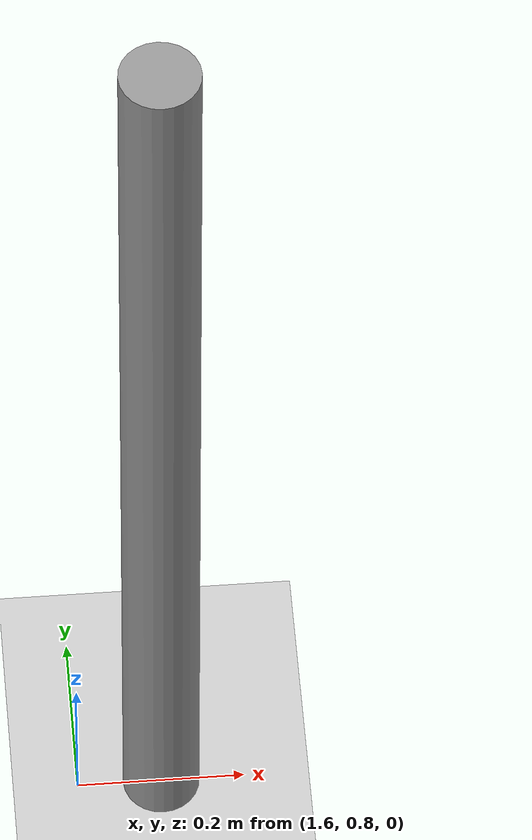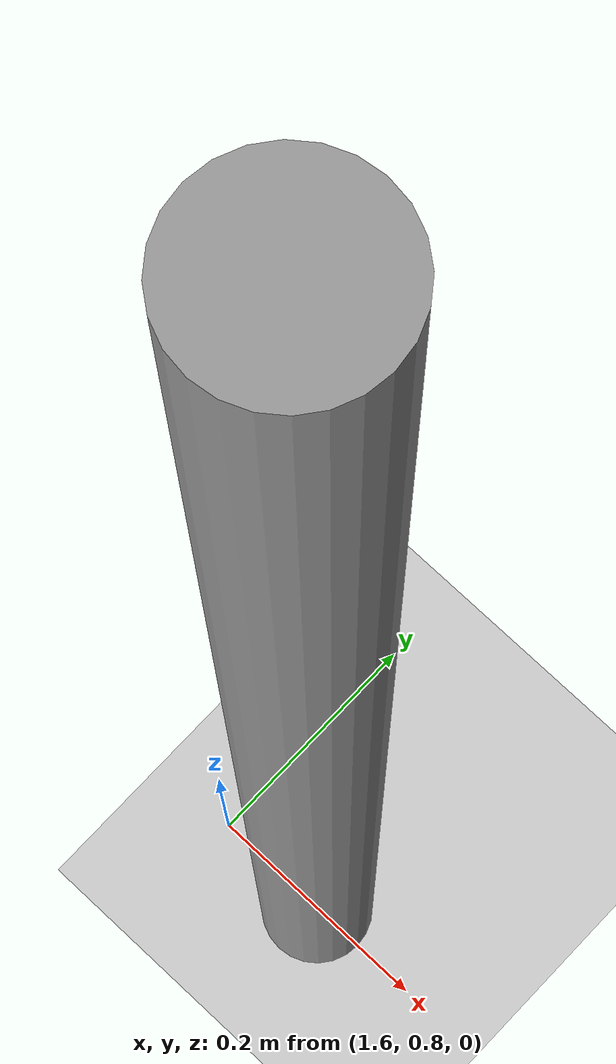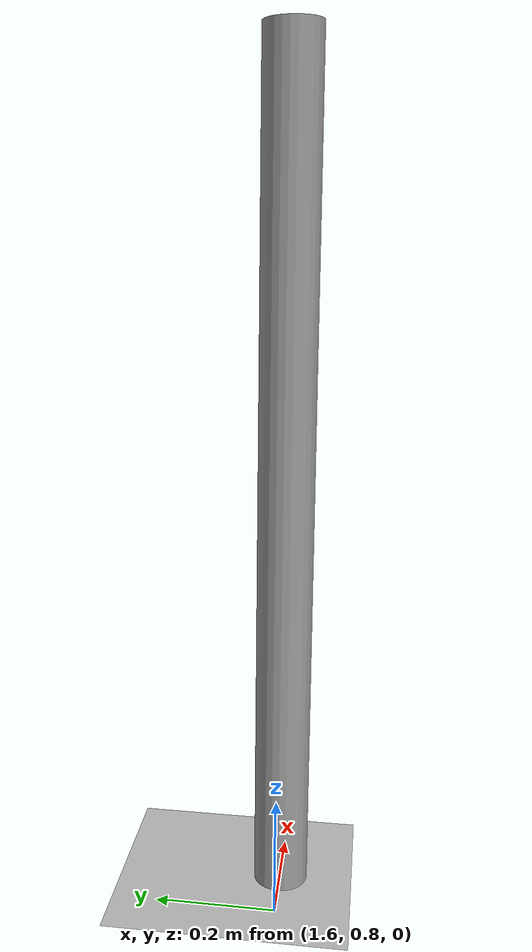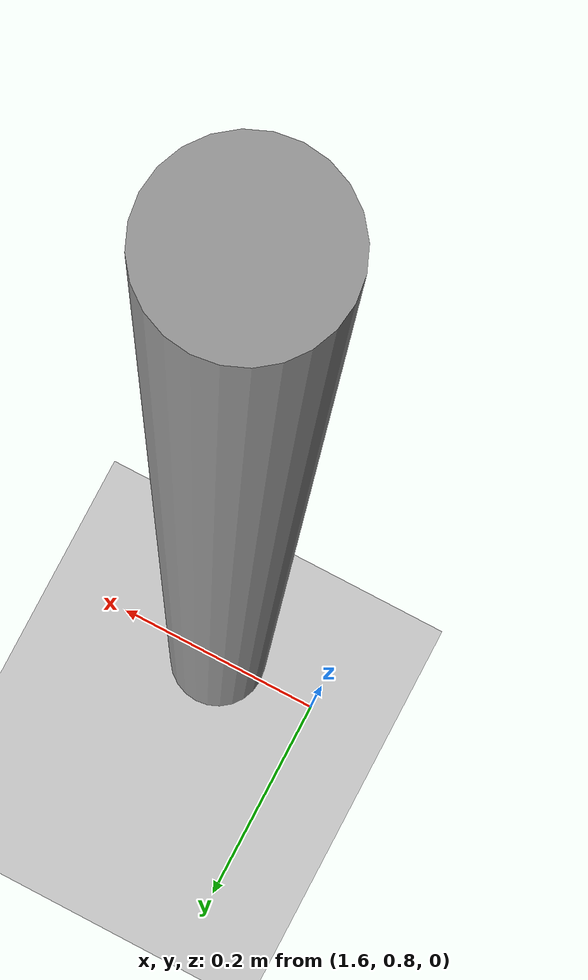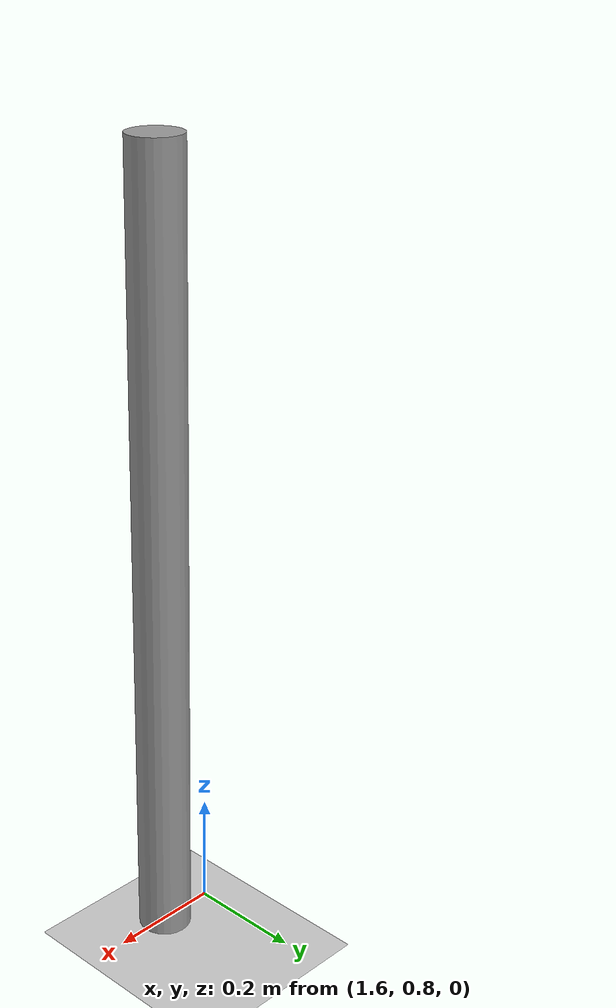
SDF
<sdf version="1.6">
 <world name="default">
  <model name="unit_cylinder_1">
   <static>0</static>
   <pose>1.7 0.8 0.691166 1e-06 5e-06 2e-06</pose>
   <link name="link">
    <inertial>
     <mass>1</mass>
     <inertia><ixz>0</ixz><ixx>1</ixx><ixy>0</ixy><izz>1</izz><iyy>1</iyy><iyz>0</iyz></inertia>
    </inertial>
    <collision name="collision">
     <geometry><cylinder><length>1.38235</length><radius>0.0456111</radius></cylinder></geometry>
    </collision>
    <visual name="visual">
     <geometry><cylinder><length>1.38235</length><radius>0.0456111</radius></cylinder></geometry>
     <material>
      <script><uri>file://media/materials/scripts/gazebo.material</uri><name>Gazebo/Grey</name></script>
     </material>
    </visual>
    <velocity_decay><linear>0</linear><angular>0</angular></velocity_decay>
   </link>
  </model>
  <model name="unit_cylinder_1">
   <static>0</static>
   <pose>1.7 0.8 0.691166 1e-06 5e-06 2e-06</pose>
   <link name="link">
    <inertial>
     <mass>1</mass>
     <inertia><ixz>0</ixz><ixx>1</ixx><ixy>0</ixy><izz>1</izz><iyy>1</iyy><iyz>0</iyz></inertia>
    </inertial>
    <collision name="collision">
     <geometry><cylinder><length>1.38235</length><radius>0.0456111</radius></cylinder></geometry>
    </collision>
    <visual name="visual">
     <geometry><cylinder><length>1.38235</length><radius>0.0456111</radius></cylinder></geometry>
     <material>
      <script><uri>file://media/materials/scripts/gazebo.material</uri><name>Gazebo/Grey</name></script>
     </material>
    </visual>
    <velocity_decay><linear>0</linear><angular>0</angular></velocity_decay>
   </link>
  </model>
  <model name="unit_cylinder_1">
   <static>0</static>
   <pose>1.7 0.8 0.691166 1e-06 5e-06 2e-06</pose>
   <link name="link">
    <inertial>
     <mass>1</mass>
     <inertia><ixz>0</ixz><ixx>1</ixx><ixy>0</ixy><izz>1</izz><iyy>1</iyy><iyz>0</iyz></inertia>
    </inertial>
    <collision name="collision">
     <geometry><cylinder><length>1.38235</length><radius>0.0456111</radius></cylinder></geometry>
    </collision>
    <visual name="visual">
     <geometry><cylinder><length>1.38235</length><radius>0.0456111</radius></cylinder></geometry>
     <material>
      <script><uri>file://media/materials/scripts/gazebo.material</uri><name>Gazebo/Grey</name></script>
     </material>
    </visual>
    <velocity_decay><linear>0</linear><angular>0</angular></velocity_decay>
   </link>
  </model>
  <model name="unit_cylinder_1">
   <static>0</static>
   <pose>1.7 0.8 0.691166 1e-06 5e-06 2e-06</pose>
   <link name="link">
    <inertial>
     <mass>1</mass>
     <inertia><ixz>0</ixz><ixx>1</ixx><ixy>0</ixy><izz>1</izz><iyy>1</iyy><iyz>0</iyz></inertia>
    </inertial>
    <collision name="collision">
     <geometry><cylinder><length>1.38235</length><radius>0.0456111</radius></cylinder></geometry>
    </collision>
    <visual name="visual">
     <geometry><cylinder><length>1.38235</length><radius>0.0456111</radius></cylinder></geometry>
     <material>
      <script><uri>file://media/materials/scripts/gazebo.material</uri><name>Gazebo/Grey</name></script>
     </material>
    </visual>
    <velocity_decay><linear>0</linear><angular>0</angular></velocity_decay>
   </link>
  </model>
  <model name="unit_cylinder_1">
   <static>0</static>
   <pose>1.7 0.8 0.691166 1e-06 5e-06 2e-06</pose>
   <link name="link">
    <inertial>
     <mass>1</mass>
     <inertia><ixz>0</ixz><ixx>1</ixx><ixy>0</ixy><izz>1</izz><iyy>1</iyy><iyz>0</iyz></inertia>
    </inertial>
    <collision name="collision">
     <geometry><cylinder><length>1.38235</length><radius>0.0456111</radius></cylinder></geometry>
    </collision>
    <visual name="visual">
     <geometry><cylinder><length>1.38235</length><radius>0.0456111</radius></cylinder></geometry>
     <material>
      <script><uri>file://media/materials/scripts/gazebo.material</uri><name>Gazebo/Grey</name></script>
     </material>
    </visual>
    <velocity_decay><linear>0</linear><angular>0</angular></velocity_decay>
   </link>
  </model>
  <model name="unit_cylinder_1">
   <static>0</static>
   <pose>1.7 0.8 0.691166 1e-06 5e-06 2e-06</pose>
   <link name="link">
    <inertial>
     <mass>1</mass>
     <inertia><ixz>0</ixz><ixx>1</ixx><ixy>0</ixy><izz>1</izz><iyy>1</iyy><iyz>0</iyz></inertia>
    </inertial>
    <collision name="collision">
     <geometry><cylinder><length>1.38235</length><radius>0.0456111</radius></cylinder></geometry>
    </collision>
    <visual name="visual">
     <geometry><cylinder><length>1.38235</length><radius>0.0456111</radius></cylinder></geometry>
     <material>
      <script><uri>file://media/materials/scripts/gazebo.material</uri><name>Gazebo/Grey</name></script>
     </material>
    </visual>
    <velocity_decay><linear>0</linear><angular>0</angular></velocity_decay>
   </link>
  </model>
  <model name="unit_cylinder_1">
   <static>0</static>
   <pose>1.7 0.8 0.691166 1e-06 5e-06 2e-06</pose>
   <link name="link">
    <inertial>
     <mass>1</mass>
     <inertia><ixz>0</ixz><ixx>1</ixx><ixy>0</ixy><izz>1</izz><iyy>1</iyy><iyz>0</iyz></inertia>
    </inertial>
    <collision name="collision">
     <geometry><cylinder><length>1.38235</length><radius>0.0456111</radius></cylinder></geometry>
    </collision>
    <visual name="visual">
     <geometry><cylinder><length>1.38235</length><radius>0.0456111</radius></cylinder></geometry>
     <material>
      <script><uri>file://media/materials/scripts/gazebo.material</uri><name>Gazebo/Grey</name></script>
     </material>
    </visual>
    <velocity_decay><linear>0</linear><angular>0</angular></velocity_decay>
   </link>
  </model>
  <model name="unit_cylinder_1">
   <static>0</static>
   <pose>1.7 0.8 0.691166 1e-06 5e-06 2e-06</pose>
   <link name="link">
    <inertial>
     <mass>1</mass>
     <inertia><ixz>0</ixz><ixx>1</ixx><ixy>0</ixy><izz>1</izz><iyy>1</iyy><iyz>0</iyz></inertia>
    </inertial>
    <collision name="collision">
     <geometry><cylinder><length>1.38235</length><radius>0.0456111</radius></cylinder></geometry>
    </collision>
    <visual name="visual">
     <geometry><cylinder><length>1.38235</length><radius>0.0456111</radius></cylinder></geometry>
     <material>
      <script><uri>file://media/materials/scripts/gazebo.material</uri><name>Gazebo/Grey</name></script>
     </material>
    </visual>
    <velocity_decay><linear>0</linear><angular>0</angular></velocity_decay>
   </link>
  </model>
  <model name="unit_cylinder_1">
   <static>0</static>
   <pose>1.7 0.8 0.691166 1e-06 5e-06 2e-06</pose>
   <link name="link">
    <inertial>
     <mass>1</mass>
     <inertia><ixz>0</ixz><ixx>1</ixx><ixy>0</ixy><izz>1</izz><iyy>1</iyy><iyz>0</iyz></inertia>
    </inertial>
    <collision name="collision">
     <geometry><cylinder><length>1.38235</length><radius>0.0456111</radius></cylinder></geometry>
    </collision>
    <visual name="visual">
     <geometry><cylinder><length>1.38235</length><radius>0.0456111</radius></cylinder></geometry>
     <material>
      <script><uri>file://media/materials/scripts/gazebo.material</uri><name>Gazebo/Grey</name></script>
     </material>
    </visual>
    <velocity_decay><linear>0</linear><angular>0</angular></velocity_decay>
   </link>
  </model>
  <model name="unit_cylinder_1">
   <static>0</static>
   <pose>1.7 0.8 0.691166 1e-06 5e-06 2e-06</pose>
   <link name="link">
    <inertial>
     <mass>1</mass>
     <inertia><ixz>0</ixz><ixx>1</ixx><ixy>0</ixy><izz>1</izz><iyy>1</iyy><iyz>0</iyz></inertia>
    </inertial>
    <collision name="collision">
     <geometry><cylinder><length>1.38235</length><radius>0.0456111</radius></cylinder></geometry>
    </collision>
    <visual name="visual">
     <geometry><cylinder><length>1.38235</length><radius>0.0456111</radius></cylinder></geometry>
     <material>
      <script><uri>file://media/materials/scripts/gazebo.material</uri><name>Gazebo/Grey</name></script>
     </material>
    </visual>
    <velocity_decay><linear>0</linear><angular>0</angular></velocity_decay>
   </link>
  </model>
  <model name="unit_cylinder_1">
   <static>0</static>
   <pose>1.7 0.8 0.691166 1e-06 5e-06 2e-06</pose>
   <link name="link">
    <inertial>
     <mass>1</mass>
     <inertia><ixz>0</ixz><ixx>1</ixx><ixy>0</ixy><izz>1</izz><iyy>1</iyy><iyz>0</iyz></inertia>
    </inertial>
    <collision name="collision">
     <geometry><cylinder><length>1.38235</length><radius>0.0456111</radius></cylinder></geometry>
    </collision>
    <visual name="visual">
     <geometry><cylinder><length>1.38235</length><radius>0.0456111</radius></cylinder></geometry>
     <material>
      <script><uri>file://media/materials/scripts/gazebo.material</uri><name>Gazebo/Grey</name></script>
     </material>
    </visual>
    <velocity_decay><linear>0</linear><angular>0</angular></velocity_decay>
   </link>
  </model>
  <model name="unit_cylinder_1">
   <static>0</static>
   <pose>1.7 0.8 0.691166 1e-06 5e-06 2e-06</pose>
   <link name="link">
    <inertial>
     <mass>1</mass>
     <inertia><ixz>0</ixz><ixx>1</ixx><ixy>0</ixy><izz>1</izz><iyy>1</iyy><iyz>0</iyz></inertia>
    </inertial>
    <collision name="collision">
     <geometry><cylinder><length>1.38235</length><radius>0.0456111</radius></cylinder></geometry>
    </collision>
    <visual name="visual">
     <geometry><cylinder><length>1.38235</length><radius>0.0456111</radius></cylinder></geometry>
     <material>
      <script><uri>file://media/materials/scripts/gazebo.material</uri><name>Gazebo/Grey</name></script>
     </material>
    </visual>
    <velocity_decay><linear>0</linear><angular>0</angular></velocity_decay>
   </link>
  </model>
  <model name="unit_cylinder_1">
   <static>0</static>
   <pose>1.7 0.8 0.691166 1e-06 5e-06 2e-06</pose>
   <link name="link">
    <inertial>
     <mass>1</mass>
     <inertia><ixz>0</ixz><ixx>1</ixx><ixy>0</ixy><izz>1</izz><iyy>1</iyy><iyz>0</iyz></inertia>
    </inertial>
    <collision name="collision">
     <geometry><cylinder><length>1.38235</length><radius>0.0456111</radius></cylinder></geometry>
    </collision>
    <visual name="visual">
     <geometry><cylinder><length>1.38235</length><radius>0.0456111</radius></cylinder></geometry>
     <material>
      <script><uri>file://media/materials/scripts/gazebo.material</uri><name>Gazebo/Grey</name></script>
     </material>
    </visual>
    <velocity_decay><linear>0</linear><angular>0</angular></velocity_decay>
   </link>
  </model>
  <model name="unit_cylinder_1">
   <static>0</static>
   <pose>1.7 0.8 0.691166 1e-06 5e-06 2e-06</pose>
   <link name="link">
    <inertial>
     <mass>1</mass>
     <inertia><ixz>0</ixz><ixx>1</ixx><ixy>0</ixy><izz>1</izz><iyy>1</iyy><iyz>0</iyz></inertia>
    </inertial>
    <collision name="collision">
     <geometry><cylinder><length>1.38235</length><radius>0.0456111</radius></cylinder></geometry>
    </collision>
    <visual name="visual">
     <geometry><cylinder><length>1.38235</length><radius>0.0456111</radius></cylinder></geometry>
     <material>
      <script><uri>file://media/materials/scripts/gazebo.material</uri><name>Gazebo/Grey</name></script>
     </material>
    </visual>
    <velocity_decay><linear>0</linear><angular>0</angular></velocity_decay>
   </link>
  </model>
  <model name="unit_cylinder_1">
   <static>0</static>
   <pose>1.7 0.8 0.691166 1e-06 5e-06 2e-06</pose>
   <link name="link">
    <inertial>
     <mass>1</mass>
     <inertia><ixz>0</ixz><ixx>1</ixx><ixy>0</ixy><izz>1</izz><iyy>1</iyy><iyz>0</iyz></inertia>
    </inertial>
    <collision name="collision">
     <geometry><cylinder><length>1.38235</length><radius>0.0456111</radius></cylinder></geometry>
    </collision>
    <visual name="visual">
     <geometry><cylinder><length>1.38235</length><radius>0.0456111</radius></cylinder></geometry>
     <material>
      <script><uri>file://media/materials/scripts/gazebo.material</uri><name>Gazebo/Grey</name></script>
     </material>
    </visual>
    <velocity_decay><linear>0</linear><angular>0</angular></velocity_decay>
   </link>
  </model>
  <model name="unit_cylinder_1">
   <static>0</static>
   <pose>1.7 0.8 0.691166 1e-06 5e-06 2e-06</pose>
   <link name="link">
    <inertial>
     <mass>1</mass>
     <inertia><ixz>0</ixz><ixx>1</ixx><ixy>0</ixy><izz>1</izz><iyy>1</iyy><iyz>0</iyz></inertia>
    </inertial>
    <collision name="collision">
     <geometry><cylinder><length>1.38235</length><radius>0.0456111</radius></cylinder></geometry>
    </collision>
    <visual name="visual">
     <geometry><cylinder><length>1.38235</length><radius>0.0456111</radius></cylinder></geometry>
     <material>
      <script><uri>file://media/materials/scripts/gazebo.material</uri><name>Gazebo/Grey</name></script>
     </material>
    </visual>
    <velocity_decay><linear>0</linear><angular>0</angular></velocity_decay>
   </link>
  </model>
  <model name="unit_cylinder_1">
   <static>0</static>
   <pose>1.7 0.8 0.691166 1e-06 5e-06 2e-06</pose>
   <link name="link">
    <inertial>
     <mass>1</mass>
     <inertia><ixz>0</ixz><ixx>1</ixx><ixy>0</ixy><izz>1</izz><iyy>1</iyy><iyz>0</iyz></inertia>
    </inertial>
    <collision name="collision">
     <geometry><cylinder><length>1.38235</length><radius>0.0456111</radius></cylinder></geometry>
    </collision>
    <visual name="visual">
     <geometry><cylinder><length>1.38235</length><radius>0.0456111</radius></cylinder></geometry>
     <material>
      <script><uri>file://media/materials/scripts/gazebo.material</uri><name>Gazebo/Grey</name></script>
     </material>
    </visual>
    <velocity_decay><linear>0</linear><angular>0</angular></velocity_decay>
   </link>
  </model>
  <model name="unit_cylinder_1">
   <static>0</static>
   <pose>1.7 0.8 0.691166 1e-06 5e-06 2e-06</pose>
   <link name="link">
    <inertial>
     <mass>1</mass>
     <inertia><ixz>0</ixz><ixx>1</ixx><ixy>0</ixy><izz>1</izz><iyy>1</iyy><iyz>0</iyz></inertia>
    </inertial>
    <collision name="collision">
     <geometry><cylinder><length>1.38235</length><radius>0.0456111</radius></cylinder></geometry>
    </collision>
    <visual name="visual">
     <geometry><cylinder><length>1.38235</length><radius>0.0456111</radius></cylinder></geometry>
     <material>
      <script><uri>file://media/materials/scripts/gazebo.material</uri><name>Gazebo/Grey</name></script>
     </material>
    </visual>
    <velocity_decay><linear>0</linear><angular>0</angular></velocity_decay>
   </link>
  </model>
  <model name="unit_cylinder_1">
   <static>0</static>
   <pose>1.7 0.8 0.691166 1e-06 5e-06 2e-06</pose>
   <link name="link">
    <inertial>
     <mass>1</mass>
     <inertia><ixz>0</ixz><ixx>1</ixx><ixy>0</ixy><izz>1</izz><iyy>1</iyy><iyz>0</iyz></inertia>
    </inertial>
    <collision name="collision">
     <geometry><cylinder><length>1.38235</length><radius>0.0456111</radius></cylinder></geometry>
    </collision>
    <visual name="visual">
     <geometry><cylinder><length>1.38235</length><radius>0.0456111</radius></cylinder></geometry>
     <material>
      <script><uri>file://media/materials/scripts/gazebo.material</uri><name>Gazebo/Grey</name></script>
     </material>
    </visual>
    <velocity_decay><linear>0</linear><angular>0</angular></velocity_decay>
   </link>
  </model>
  <model name="unit_cylinder_1">
   <static>0</static>
   <pose>1.7 0.8 0.691166 1e-06 5e-06 2e-06</pose>
   <link name="link">
    <inertial>
     <mass>1</mass>
     <inertia><ixz>0</ixz><ixx>1</ixx><ixy>0</ixy><izz>1</izz><iyy>1</iyy><iyz>0</iyz></inertia>
    </inertial>
    <collision name="collision">
     <geometry><cylinder><length>1.38235</length><radius>0.0456111</radius></cylinder></geometry>
    </collision>
    <visual name="visual">
     <geometry><cylinder><length>1.38235</length><radius>0.0456111</radius></cylinder></geometry>
     <material>
      <script><uri>file://media/materials/scripts/gazebo.material</uri><name>Gazebo/Grey</name></script>
     </material>
    </visual>
    <velocity_decay><linear>0</linear><angular>0</angular></velocity_decay>
   </link>
  </model>
  <model name="unit_cylinder_1">
   <static>0</static>
   <pose>1.7 0.8 0.691166 1e-06 5e-06 2e-06</pose>
   <link name="link">
    <inertial>
     <mass>1</mass>
     <inertia><ixz>0</ixz><ixx>1</ixx><ixy>0</ixy><izz>1</izz><iyy>1</iyy><iyz>0</iyz></inertia>
    </inertial>
    <collision name="collision">
     <geometry><cylinder><length>1.38235</length><radius>0.0456111</radius></cylinder></geometry>
    </collision>
    <visual name="visual">
     <geometry><cylinder><length>1.38235</length><radius>0.0456111</radius></cylinder></geometry>
     <material>
      <script><uri>file://media/materials/scripts/gazebo.material</uri><name>Gazebo/Grey</name></script>
     </material>
    </visual>
    <velocity_decay><linear>0</linear><angular>0</angular></velocity_decay>
   </link>
  </model>
  <model name="unit_cylinder_1">
   <static>0</static>
   <pose>1.7 0.8 0.691166 1e-06 5e-06 2e-06</pose>
   <link name="link">
    <inertial>
     <mass>1</mass>
     <inertia><ixz>0</ixz><ixx>1</ixx><ixy>0</ixy><izz>1</izz><iyy>1</iyy><iyz>0</iyz></inertia>
    </inertial>
    <collision name="collision">
     <geometry><cylinder><length>1.38235</length><radius>0.0456111</radius></cylinder></geometry>
    </collision>
    <visual name="visual">
     <geometry><cylinder><length>1.38235</length><radius>0.0456111</radius></cylinder></geometry>
     <material>
      <script><uri>file://media/materials/scripts/gazebo.material</uri><name>Gazebo/Grey</name></script>
     </material>
    </visual>
    <velocity_decay><linear>0</linear><angular>0</angular></velocity_decay>
   </link>
  </model>
  <model name="unit_cylinder_1">
   <static>0</static>
   <pose>1.7 0.8 0.691166 1e-06 5e-06 2e-06</pose>
   <link name="link">
    <inertial>
     <mass>1</mass>
     <inertia><ixz>0</ixz><ixx>1</ixx><ixy>0</ixy><izz>1</izz><iyy>1</iyy><iyz>0</iyz></inertia>
    </inertial>
    <collision name="collision">
     <geometry><cylinder><length>1.38235</length><radius>0.0456111</radius></cylinder></geometry>
    </collision>
    <visual name="visual">
     <geometry><cylinder><length>1.38235</length><radius>0.0456111</radius></cylinder></geometry>
     <material>
      <script><uri>file://media/materials/scripts/gazebo.material</uri><name>Gazebo/Grey</name></script>
     </material>
    </visual>
    <velocity_decay><linear>0</linear><angular>0</angular></velocity_decay>
   </link>
  </model>
  <model name="unit_cylinder_1">
   <static>0</static>
   <pose>1.7 0.8 0.691166 1e-06 5e-06 2e-06</pose>
   <link name="link">
    <inertial>
     <mass>1</mass>
     <inertia><ixz>0</ixz><ixx>1</ixx><ixy>0</ixy><izz>1</izz><iyy>1</iyy><iyz>0</iyz></inertia>
    </inertial>
    <collision name="collision">
     <geometry><cylinder><length>1.38235</length><radius>0.0456111</radius></cylinder></geometry>
    </collision>
    <visual name="visual">
     <geometry><cylinder><length>1.38235</length><radius>0.0456111</radius></cylinder></geometry>
     <material>
      <script><uri>file://media/materials/scripts/gazebo.material</uri><name>Gazebo/Grey</name></script>
     </material>
    </visual>
    <velocity_decay><linear>0</linear><angular>0</angular></velocity_decay>
   </link>
  </model>
  <model name="unit_cylinder_1">
   <static>0</static>
   <pose>1.7 0.8 0.691166 1e-06 5e-06 2e-06</pose>
   <link name="link">
    <inertial>
     <mass>1</mass>
     <inertia><ixz>0</ixz><ixx>1</ixx><ixy>0</ixy><izz>1</izz><iyy>1</iyy><iyz>0</iyz></inertia>
    </inertial>
    <collision name="collision">
     <geometry><cylinder><length>1.38235</length><radius>0.0456111</radius></cylinder></geometry>
    </collision>
    <visual name="visual">
     <geometry><cylinder><length>1.38235</length><radius>0.0456111</radius></cylinder></geometry>
     <material>
      <script><uri>file://media/materials/scripts/gazebo.material</uri><name>Gazebo/Grey</name></script>
     </material>
    </visual>
    <velocity_decay><linear>0</linear><angular>0</angular></velocity_decay>
   </link>
  </model>
  <model name="unit_cylinder_1">
   <static>0</static>
   <pose>1.7 0.8 0.691166 1e-06 5e-06 2e-06</pose>
   <link name="link">
    <inertial>
     <mass>1</mass>
     <inertia><ixz>0</ixz><ixx>1</ixx><ixy>0</ixy><izz>1</izz><iyy>1</iyy><iyz>0</iyz></inertia>
    </inertial>
    <collision name="collision">
     <geometry><cylinder><length>1.38235</length><radius>0.0456111</radius></cylinder></geometry>
    </collision>
    <visual name="visual">
     <geometry><cylinder><length>1.38235</length><radius>0.0456111</radius></cylinder></geometry>
     <material>
      <script><uri>file://media/materials/scripts/gazebo.material</uri><name>Gazebo/Grey</name></script>
     </material>
    </visual>
    <velocity_decay><linear>0</linear><angular>0</angular></velocity_decay>
   </link>
  </model>
  <model name="unit_cylinder_1">
   <static>0</static>
   <pose>1.7 0.8 0.691166 1e-06 5e-06 2e-06</pose>
   <link name="link">
    <inertial>
     <mass>1</mass>
     <inertia><ixz>0</ixz><ixx>1</ixx><ixy>0</ixy><izz>1</izz><iyy>1</iyy><iyz>0</iyz></inertia>
    </inertial>
    <collision name="collision">
     <geometry><cylinder><length>1.38235</length><radius>0.0456111</radius></cylinder></geometry>
    </collision>
    <visual name="visual">
     <geometry><cylinder><length>1.38235</length><radius>0.0456111</radius></cylinder></geometry>
     <material>
      <script><uri>file://media/materials/scripts/gazebo.material</uri><name>Gazebo/Grey</name></script>
     </material>
    </visual>
    <velocity_decay><linear>0</linear><angular>0</angular></velocity_decay>
   </link>
  </model>
  <model name="unit_cylinder_1">
   <static>0</static>
   <pose>1.7 0.8 0.691166 1e-06 5e-06 2e-06</pose>
   <link name="link">
    <inertial>
     <mass>1</mass>
     <inertia><ixz>0</ixz><ixx>1</ixx><ixy>0</ixy><izz>1</izz><iyy>1</iyy><iyz>0</iyz></inertia>
    </inertial>
    <collision name="collision">
     <geometry><cylinder><length>1.38235</length><radius>0.0456111</radius></cylinder></geometry>
    </collision>
    <visual name="visual">
     <geometry><cylinder><length>1.38235</length><radius>0.0456111</radius></cylinder></geometry>
     <material>
      <script><uri>file://media/materials/scripts/gazebo.material</uri><name>Gazebo/Grey</name></script>
     </material>
    </visual>
    <velocity_decay><linear>0</linear><angular>0</angular></velocity_decay>
   </link>
  </model>
  <model name="unit_cylinder_1">
   <static>0</static>
   <pose>1.7 0.8 0.691166 1e-06 5e-06 2e-06</pose>
   <link name="link">
    <inertial>
     <mass>1</mass>
     <inertia><ixz>0</ixz><ixx>1</ixx><ixy>0</ixy><izz>1</izz><iyy>1</iyy><iyz>0</iyz></inertia>
    </inertial>
    <collision name="collision">
     <geometry><cylinder><length>1.38235</length><radius>0.0456111</radius></cylinder></geometry>
    </collision>
    <visual name="visual">
     <geometry><cylinder><length>1.38235</length><radius>0.0456111</radius></cylinder></geometry>
     <material>
      <script><uri>file://media/materials/scripts/gazebo.material</uri><name>Gazebo/Grey</name></script>
     </material>
    </visual>
    <velocity_decay><linear>0</linear><angular>0</angular></velocity_decay>
   </link>
  </model>
  <model name="unit_cylinder_1">
   <static>0</static>
   <pose>1.7 0.8 0.691166 1e-06 5e-06 2e-06</pose>
   <link name="link">
    <inertial>
     <mass>1</mass>
     <inertia><ixz>0</ixz><ixx>1</ixx><ixy>0</ixy><izz>1</izz><iyy>1</iyy><iyz>0</iyz></inertia>
    </inertial>
    <collision name="collision">
     <geometry><cylinder><length>1.38235</length><radius>0.0456111</radius></cylinder></geometry>
    </collision>
    <visual name="visual">
     <geometry><cylinder><length>1.38235</length><radius>0.0456111</radius></cylinder></geometry>
     <material>
      <script><uri>file://media/materials/scripts/gazebo.material</uri><name>Gazebo/Grey</name></script>
     </material>
    </visual>
    <velocity_decay><linear>0</linear><angular>0</angular></velocity_decay>
   </link>
  </model>
  <model name="unit_cylinder_1">
   <static>0</static>
   <pose>1.7 0.8 0.691166 1e-06 5e-06 2e-06</pose>
   <link name="link">
    <inertial>
     <mass>1</mass>
     <inertia><ixz>0</ixz><ixx>1</ixx><ixy>0</ixy><izz>1</izz><iyy>1</iyy><iyz>0</iyz></inertia>
    </inertial>
    <collision name="collision">
     <geometry><cylinder><length>1.38235</length><radius>0.0456111</radius></cylinder></geometry>
    </collision>
    <visual name="visual">
     <geometry><cylinder><length>1.38235</length><radius>0.0456111</radius></cylinder></geometry>
     <material>
      <script><uri>file://media/materials/scripts/gazebo.material</uri><name>Gazebo/Grey</name></script>
     </material>
    </visual>
    <velocity_decay><linear>0</linear><angular>0</angular></velocity_decay>
   </link>
  </model>
  <model name="unit_cylinder_1">
   <static>0</static>
   <pose>1.7 0.8 0.691166 1e-06 5e-06 2e-06</pose>
   <link name="link">
    <inertial>
     <mass>1</mass>
     <inertia><ixz>0</ixz><ixx>1</ixx><ixy>0</ixy><izz>1</izz><iyy>1</iyy><iyz>0</iyz></inertia>
    </inertial>
    <collision name="collision">
     <geometry><cylinder><length>1.38235</length><radius>0.0456111</radius></cylinder></geometry>
    </collision>
    <visual name="visual">
     <geometry><cylinder><length>1.38235</length><radius>0.0456111</radius></cylinder></geometry>
     <material>
      <script><uri>file://media/materials/scripts/gazebo.material</uri><name>Gazebo/Grey</name></script>
     </material>
    </visual>
    <velocity_decay><linear>0</linear><angular>0</angular></velocity_decay>
   </link>
  </model>
  <model name="unit_cylinder_1">
   <static>0</static>
   <pose>1.7 0.8 0.691166 1e-06 5e-06 2e-06</pose>
   <link name="link">
    <inertial>
     <mass>1</mass>
     <inertia><ixz>0</ixz><ixx>1</ixx><ixy>0</ixy><izz>1</izz><iyy>1</iyy><iyz>0</iyz></inertia>
    </inertial>
    <collision name="collision">
     <geometry><cylinder><length>1.38235</length><radius>0.0456111</radius></cylinder></geometry>
    </collision>
    <visual name="visual">
     <geometry><cylinder><length>1.38235</length><radius>0.0456111</radius></cylinder></geometry>
     <material>
      <script><uri>file://media/materials/scripts/gazebo.material</uri><name>Gazebo/Grey</name></script>
     </material>
    </visual>
    <velocity_decay><linear>0</linear><angular>0</angular></velocity_decay>
   </link>
  </model>
  <model name="unit_cylinder_1">
   <static>0</static>
   <pose>1.7 0.8 0.691166 1e-06 5e-06 2e-06</pose>
   <link name="link">
    <inertial>
     <mass>1</mass>
     <inertia><ixz>0</ixz><ixx>1</ixx><ixy>0</ixy><izz>1</izz><iyy>1</iyy><iyz>0</iyz></inertia>
    </inertial>
    <collision name="collision">
     <geometry><cylinder><length>1.38235</length><radius>0.0456111</radius></cylinder></geometry>
    </collision>
    <visual name="visual">
     <geometry><cylinder><length>1.38235</length><radius>0.0456111</radius></cylinder></geometry>
     <material>
      <script><uri>file://media/materials/scripts/gazebo.material</uri><name>Gazebo/Grey</name></script>
     </material>
    </visual>
    <velocity_decay><linear>0</linear><angular>0</angular></velocity_decay>
   </link>
  </model>
  <model name="unit_cylinder_1">
   <static>0</static>
   <pose>1.7 0.8 0.691166 1e-06 5e-06 2e-06</pose>
   <link name="link">
    <inertial>
     <mass>1</mass>
     <inertia><ixz>0</ixz><ixx>1</ixx><ixy>0</ixy><izz>1</izz><iyy>1</iyy><iyz>0</iyz></inertia>
    </inertial>
    <collision name="collision">
     <geometry><cylinder><length>1.38235</length><radius>0.0456111</radius></cylinder></geometry>
    </collision>
    <visual name="visual">
     <geometry><cylinder><length>1.38235</length><radius>0.0456111</radius></cylinder></geometry>
     <material>
      <script><uri>file://media/materials/scripts/gazebo.material</uri><name>Gazebo/Grey</name></script>
     </material>
    </visual>
    <velocity_decay><linear>0</linear><angular>0</angular></velocity_decay>
   </link>
  </model>
  <model name="unit_cylinder_1">
   <static>0</static>
   <pose>1.7 0.8 0.691166 1e-06 5e-06 2e-06</pose>
   <link name="link">
    <inertial>
     <mass>1</mass>
     <inertia><ixz>0</ixz><ixx>1</ixx><ixy>0</ixy><izz>1</izz><iyy>1</iyy><iyz>0</iyz></inertia>
    </inertial>
    <collision name="collision">
     <geometry><cylinder><length>1.38235</length><radius>0.0456111</radius></cylinder></geometry>
    </collision>
    <visual name="visual">
     <geometry><cylinder><length>1.38235</length><radius>0.0456111</radius></cylinder></geometry>
     <material>
      <script><uri>file://media/materials/scripts/gazebo.material</uri><name>Gazebo/Grey</name></script>
     </material>
    </visual>
    <velocity_decay><linear>0</linear><angular>0</angular></velocity_decay>
   </link>
  </model>
  <model name="unit_cylinder_1">
   <static>0</static>
   <pose>1.7 0.8 0.691166 1e-06 5e-06 2e-06</pose>
   <link name="link">
    <inertial>
     <mass>1</mass>
     <inertia><ixz>0</ixz><ixx>1</ixx><ixy>0</ixy><izz>1</izz><iyy>1</iyy><iyz>0</iyz></inertia>
    </inertial>
    <collision name="collision">
     <geometry><cylinder><length>1.38235</length><radius>0.0456111</radius></cylinder></geometry>
    </collision>
    <visual name="visual">
     <geometry><cylinder><length>1.38235</length><radius>0.0456111</radius></cylinder></geometry>
     <material>
      <script><uri>file://media/materials/scripts/gazebo.material</uri><name>Gazebo/Grey</name></script>
     </material>
    </visual>
    <velocity_decay><linear>0</linear><angular>0</angular></velocity_decay>
   </link>
  </model>
  <model name="unit_cylinder_1">
   <static>0</static>
   <pose>1.7 0.8 0.691166 1e-06 5e-06 2e-06</pose>
   <link name="link">
    <inertial>
     <mass>1</mass>
     <inertia><ixz>0</ixz><ixx>1</ixx><ixy>0</ixy><izz>1</izz><iyy>1</iyy><iyz>0</iyz></inertia>
    </inertial>
    <collision name="collision">
     <geometry><cylinder><length>1.38235</length><radius>0.0456111</radius></cylinder></geometry>
    </collision>
    <visual name="visual">
     <geometry><cylinder><length>1.38235</length><radius>0.0456111</radius></cylinder></geometry>
     <material>
      <script><uri>file://media/materials/scripts/gazebo.material</uri><name>Gazebo/Grey</name></script>
     </material>
    </visual>
    <velocity_decay><linear>0</linear><angular>0</angular></velocity_decay>
   </link>
  </model>
  <model name="unit_cylinder_1">
   <static>0</static>
   <pose>1.7 0.8 0.691166 1e-06 5e-06 2e-06</pose>
   <link name="link">
    <inertial>
     <mass>1</mass>
     <inertia><ixz>0</ixz><ixx>1</ixx><ixy>0</ixy><izz>1</izz><iyy>1</iyy><iyz>0</iyz></inertia>
    </inertial>
    <collision name="collision">
     <geometry><cylinder><length>1.38235</length><radius>0.0456111</radius></cylinder></geometry>
    </collision>
    <visual name="visual">
     <geometry><cylinder><length>1.38235</length><radius>0.0456111</radius></cylinder></geometry>
     <material>
      <script><uri>file://media/materials/scripts/gazebo.material</uri><name>Gazebo/Grey</name></script>
     </material>
    </visual>
    <velocity_decay><linear>0</linear><angular>0</angular></velocity_decay>
   </link>
  </model>
  <model name="unit_cylinder_1">
   <static>0</static>
   <pose>1.7 0.8 0.691166 1e-06 5e-06 2e-06</pose>
   <link name="link">
    <inertial>
     <mass>1</mass>
     <inertia><ixz>0</ixz><ixx>1</ixx><ixy>0</ixy><izz>1</izz><iyy>1</iyy><iyz>0</iyz></inertia>
    </inertial>
    <collision name="collision">
     <geometry><cylinder><length>1.38235</length><radius>0.0456111</radius></cylinder></geometry>
    </collision>
    <visual name="visual">
     <geometry><cylinder><length>1.38235</length><radius>0.0456111</radius></cylinder></geometry>
     <material>
      <script><uri>file://media/materials/scripts/gazebo.material</uri><name>Gazebo/Grey</name></script>
     </material>
    </visual>
    <velocity_decay><linear>0</linear><angular>0</angular></velocity_decay>
   </link>
  </model>
  <model name="unit_cylinder_1">
   <static>0</static>
   <pose>1.7 0.8 0.691166 1e-06 5e-06 2e-06</pose>
   <link name="link">
    <inertial>
     <mass>1</mass>
     <inertia><ixz>0</ixz><ixx>1</ixx><ixy>0</ixy><izz>1</izz><iyy>1</iyy><iyz>0</iyz></inertia>
    </inertial>
    <collision name="collision">
     <geometry><cylinder><length>1.38235</length><radius>0.0456111</radius></cylinder></geometry>
    </collision>
    <visual name="visual">
     <geometry><cylinder><length>1.38235</length><radius>0.0456111</radius></cylinder></geometry>
     <material>
      <script><uri>file://media/materials/scripts/gazebo.material</uri><name>Gazebo/Grey</name></script>
     </material>
    </visual>
    <velocity_decay><linear>0</linear><angular>0</angular></velocity_decay>
   </link>
  </model>
  <model name="unit_cylinder_1">
   <static>0</static>
   <pose>1.7 0.8 0.691166 1e-06 5e-06 2e-06</pose>
   <link name="link">
    <inertial>
     <mass>1</mass>
     <inertia><ixz>0</ixz><ixx>1</ixx><ixy>0</ixy><izz>1</izz><iyy>1</iyy><iyz>0</iyz></inertia>
    </inertial>
    <collision name="collision">
     <geometry><cylinder><length>1.38235</length><radius>0.0456111</radius></cylinder></geometry>
    </collision>
    <visual name="visual">
     <geometry><cylinder><length>1.38235</length><radius>0.0456111</radius></cylinder></geometry>
     <material>
      <script><uri>file://media/materials/scripts/gazebo.material</uri><name>Gazebo/Grey</name></script>
     </material>
    </visual>
    <velocity_decay><linear>0</linear><angular>0</angular></velocity_decay>
   </link>
  </model>
  <model name="unit_cylinder_1">
   <static>0</static>
   <pose>1.7 0.8 0.691166 1e-06 5e-06 2e-06</pose>
   <link name="link">
    <inertial>
     <mass>1</mass>
     <inertia><ixz>0</ixz><ixx>1</ixx><ixy>0</ixy><izz>1</izz><iyy>1</iyy><iyz>0</iyz></inertia>
    </inertial>
    <collision name="collision">
     <geometry><cylinder><length>1.38235</length><radius>0.0456111</radius></cylinder></geometry>
    </collision>
    <visual name="visual">
     <geometry><cylinder><length>1.38235</length><radius>0.0456111</radius></cylinder></geometry>
     <material>
      <script><uri>file://media/materials/scripts/gazebo.material</uri><name>Gazebo/Grey</name></script>
     </material>
    </visual>
    <velocity_decay><linear>0</linear><angular>0</angular></velocity_decay>
   </link>
  </model>
  <model name="unit_cylinder_1">
   <static>0</static>
   <pose>1.7 0.8 0.691166 1e-06 5e-06 2e-06</pose>
   <link name="link">
    <inertial>
     <mass>1</mass>
     <inertia><ixz>0</ixz><ixx>1</ixx><ixy>0</ixy><izz>1</izz><iyy>1</iyy><iyz>0</iyz></inertia>
    </inertial>
    <collision name="collision">
     <geometry><cylinder><length>1.38235</length><radius>0.0456111</radius></cylinder></geometry>
    </collision>
    <visual name="visual">
     <geometry><cylinder><length>1.38235</length><radius>0.0456111</radius></cylinder></geometry>
     <material>
      <script><uri>file://media/materials/scripts/gazebo.material</uri><name>Gazebo/Grey</name></script>
     </material>
    </visual>
    <velocity_decay><linear>0</linear><angular>0</angular></velocity_decay>
   </link>
  </model>
  <model name="unit_cylinder_1">
   <static>0</static>
   <pose>1.7 0.8 0.691166 1e-06 5e-06 2e-06</pose>
   <link name="link">
    <inertial>
     <mass>1</mass>
     <inertia><ixz>0</ixz><ixx>1</ixx><ixy>0</ixy><izz>1</izz><iyy>1</iyy><iyz>0</iyz></inertia>
    </inertial>
    <collision name="collision">
     <geometry><cylinder><length>1.38235</length><radius>0.0456111</radius></cylinder></geometry>
    </collision>
    <visual name="visual">
     <geometry><cylinder><length>1.38235</length><radius>0.0456111</radius></cylinder></geometry>
     <material>
      <script><uri>file://media/materials/scripts/gazebo.material</uri><name>Gazebo/Grey</name></script>
     </material>
    </visual>
    <velocity_decay><linear>0</linear><angular>0</angular></velocity_decay>
   </link>
  </model>
  <model name="unit_cylinder_1">
   <static>0</static>
   <pose>1.7 0.8 0.691166 1e-06 5e-06 2e-06</pose>
   <link name="link">
    <inertial>
     <mass>1</mass>
     <inertia><ixz>0</ixz><ixx>1</ixx><ixy>0</ixy><izz>1</izz><iyy>1</iyy><iyz>0</iyz></inertia>
    </inertial>
    <collision name="collision">
     <geometry><cylinder><length>1.38235</length><radius>0.0456111</radius></cylinder></geometry>
    </collision>
    <visual name="visual">
     <geometry><cylinder><length>1.38235</length><radius>0.0456111</radius></cylinder></geometry>
     <material>
      <script><uri>file://media/materials/scripts/gazebo.material</uri><name>Gazebo/Grey</name></script>
     </material>
    </visual>
    <velocity_decay><linear>0</linear><angular>0</angular></velocity_decay>
   </link>
  </model>
  <model name="unit_cylinder_1">
   <static>0</static>
   <pose>1.7 0.8 0.691166 1e-06 5e-06 2e-06</pose>
   <link name="link">
    <inertial>
     <mass>1</mass>
     <inertia><ixz>0</ixz><ixx>1</ixx><ixy>0</ixy><izz>1</izz><iyy>1</iyy><iyz>0</iyz></inertia>
    </inertial>
    <collision name="collision">
     <geometry><cylinder><length>1.38235</length><radius>0.0456111</radius></cylinder></geometry>
    </collision>
    <visual name="visual">
     <geometry><cylinder><length>1.38235</length><radius>0.0456111</radius></cylinder></geometry>
     <material>
      <script><uri>file://media/materials/scripts/gazebo.material</uri><name>Gazebo/Grey</name></script>
     </material>
    </visual>
    <velocity_decay><linear>0</linear><angular>0</angular></velocity_decay>
   </link>
  </model>
  <model name="unit_cylinder_1">
   <static>0</static>
   <pose>1.7 0.8 0.691166 1e-06 5e-06 2e-06</pose>
   <link name="link">
    <inertial>
     <mass>1</mass>
     <inertia><ixz>0</ixz><ixx>1</ixx><ixy>0</ixy><izz>1</izz><iyy>1</iyy><iyz>0</iyz></inertia>
    </inertial>
    <collision name="collision">
     <geometry><cylinder><length>1.38235</length><radius>0.0456111</radius></cylinder></geometry>
    </collision>
    <visual name="visual">
     <geometry><cylinder><length>1.38235</length><radius>0.0456111</radius></cylinder></geometry>
     <material>
      <script><uri>file://media/materials/scripts/gazebo.material</uri><name>Gazebo/Grey</name></script>
     </material>
    </visual>
    <velocity_decay><linear>0</linear><angular>0</angular></velocity_decay>
   </link>
  </model>
  <model name="unit_cylinder_1">
   <static>0</static>
   <pose>1.7 0.8 0.691166 1e-06 5e-06 2e-06</pose>
   <link name="link">
    <inertial>
     <mass>1</mass>
     <inertia><ixz>0</ixz><ixx>1</ixx><ixy>0</ixy><izz>1</izz><iyy>1</iyy><iyz>0</iyz></inertia>
    </inertial>
    <collision name="collision">
     <geometry><cylinder><length>1.38235</length><radius>0.0456111</radius></cylinder></geometry>
    </collision>
    <visual name="visual">
     <geometry><cylinder><length>1.38235</length><radius>0.0456111</radius></cylinder></geometry>
     <material>
      <script><uri>file://media/materials/scripts/gazebo.material</uri><name>Gazebo/Grey</name></script>
     </material>
    </visual>
    <velocity_decay><linear>0</linear><angular>0</angular></velocity_decay>
   </link>
  </model>
  <model name="unit_cylinder_1">
   <static>0</static>
   <pose>1.7 0.8 0.691166 1e-06 5e-06 2e-06</pose>
   <link name="link">
    <inertial>
     <mass>1</mass>
     <inertia><ixz>0</ixz><ixx>1</ixx><ixy>0</ixy><izz>1</izz><iyy>1</iyy><iyz>0</iyz></inertia>
    </inertial>
    <collision name="collision">
     <geometry><cylinder><length>1.38235</length><radius>0.0456111</radius></cylinder></geometry>
    </collision>
    <visual name="visual">
     <geometry><cylinder><length>1.38235</length><radius>0.0456111</radius></cylinder></geometry>
     <material>
      <script><uri>file://media/materials/scripts/gazebo.material</uri><name>Gazebo/Grey</name></script>
     </material>
    </visual>
    <velocity_decay><linear>0</linear><angular>0</angular></velocity_decay>
   </link>
  </model>
  <model name="unit_cylinder_1">
   <static>0</static>
   <pose>1.7 0.8 0.691166 1e-06 5e-06 2e-06</pose>
   <link name="link">
    <inertial>
     <mass>1</mass>
     <inertia><ixz>0</ixz><ixx>1</ixx><ixy>0</ixy><izz>1</izz><iyy>1</iyy><iyz>0</iyz></inertia>
    </inertial>
    <collision name="collision">
     <geometry><cylinder><length>1.38235</length><radius>0.0456111</radius></cylinder></geometry>
    </collision>
    <visual name="visual">
     <geometry><cylinder><length>1.38235</length><radius>0.0456111</radius></cylinder></geometry>
     <material>
      <script><uri>file://media/materials/scripts/gazebo.material</uri><name>Gazebo/Grey</name></script>
     </material>
    </visual>
    <velocity_decay><linear>0</linear><angular>0</angular></velocity_decay>
   </link>
  </model>
  <model name="unit_cylinder_1">
   <static>0</static>
   <pose>1.7 0.8 0.691166 1e-06 5e-06 2e-06</pose>
   <link name="link">
    <inertial>
     <mass>1</mass>
     <inertia><ixz>0</ixz><ixx>1</ixx><ixy>0</ixy><izz>1</izz><iyy>1</iyy><iyz>0</iyz></inertia>
    </inertial>
    <collision name="collision">
     <geometry><cylinder><length>1.38235</length><radius>0.0456111</radius></cylinder></geometry>
    </collision>
    <visual name="visual">
     <geometry><cylinder><length>1.38235</length><radius>0.0456111</radius></cylinder></geometry>
     <material>
      <script><uri>file://media/materials/scripts/gazebo.material</uri><name>Gazebo/Grey</name></script>
     </material>
    </visual>
    <velocity_decay><linear>0</linear><angular>0</angular></velocity_decay>
   </link>
  </model>
  <model name="unit_cylinder_1">
   <static>0</static>
   <pose>1.7 0.8 0.691166 1e-06 5e-06 2e-06</pose>
   <link name="link">
    <inertial>
     <mass>1</mass>
     <inertia><ixz>0</ixz><ixx>1</ixx><ixy>0</ixy><izz>1</izz><iyy>1</iyy><iyz>0</iyz></inertia>
    </inertial>
    <collision name="collision">
     <geometry><cylinder><length>1.38235</length><radius>0.0456111</radius></cylinder></geometry>
    </collision>
    <visual name="visual">
     <geometry><cylinder><length>1.38235</length><radius>0.0456111</radius></cylinder></geometry>
     <material>
      <script><uri>file://media/materials/scripts/gazebo.material</uri><name>Gazebo/Grey</name></script>
     </material>
    </visual>
    <velocity_decay><linear>0</linear><angular>0</angular></velocity_decay>
   </link>
  </model>
  <model name="unit_cylinder_1">
   <static>0</static>
   <pose>1.7 0.8 0.691166 1e-06 5e-06 2e-06</pose>
   <link name="link">
    <inertial>
     <mass>1</mass>
     <inertia><ixz>0</ixz><ixx>1</ixx><ixy>0</ixy><izz>1</izz><iyy>1</iyy><iyz>0</iyz></inertia>
    </inertial>
    <collision name="collision">
     <geometry><cylinder><length>1.38235</length><radius>0.0456111</radius></cylinder></geometry>
    </collision>
    <visual name="visual">
     <geometry><cylinder><length>1.38235</length><radius>0.0456111</radius></cylinder></geometry>
     <material>
      <script><uri>file://media/materials/scripts/gazebo.material</uri><name>Gazebo/Grey</name></script>
     </material>
    </visual>
    <velocity_decay><linear>0</linear><angular>0</angular></velocity_decay>
   </link>
  </model>
  <model name="unit_cylinder_1">
   <static>0</static>
   <pose>1.7 0.8 0.691166 1e-06 5e-06 2e-06</pose>
   <link name="link">
    <inertial>
     <mass>1</mass>
     <inertia><ixz>0</ixz><ixx>1</ixx><ixy>0</ixy><izz>1</izz><iyy>1</iyy><iyz>0</iyz></inertia>
    </inertial>
    <collision name="collision">
     <geometry><cylinder><length>1.38235</length><radius>0.0456111</radius></cylinder></geometry>
    </collision>
    <visual name="visual">
     <geometry><cylinder><length>1.38235</length><radius>0.0456111</radius></cylinder></geometry>
     <material>
      <script><uri>file://media/materials/scripts/gazebo.material</uri><name>Gazebo/Grey</name></script>
     </material>
    </visual>
    <velocity_decay><linear>0</linear><angular>0</angular></velocity_decay>
   </link>
  </model>
  <model name="unit_cylinder_1">
   <static>0</static>
   <pose>1.7 0.8 0.691166 1e-06 5e-06 2e-06</pose>
   <link name="link">
    <inertial>
     <mass>1</mass>
     <inertia><ixz>0</ixz><ixx>1</ixx><ixy>0</ixy><izz>1</izz><iyy>1</iyy><iyz>0</iyz></inertia>
    </inertial>
    <collision name="collision">
     <geometry><cylinder><length>1.38235</length><radius>0.0456111</radius></cylinder></geometry>
    </collision>
    <visual name="visual">
     <geometry><cylinder><length>1.38235</length><radius>0.0456111</radius></cylinder></geometry>
     <material>
      <script><uri>file://media/materials/scripts/gazebo.material</uri><name>Gazebo/Grey</name></script>
     </material>
    </visual>
    <velocity_decay><linear>0</linear><angular>0</angular></velocity_decay>
   </link>
  </model>
  <model name="unit_cylinder_1">
   <static>0</static>
   <pose>1.7 0.8 0.691166 1e-06 5e-06 2e-06</pose>
   <link name="link">
    <inertial>
     <mass>1</mass>
     <inertia><ixz>0</ixz><ixx>1</ixx><ixy>0</ixy><izz>1</izz><iyy>1</iyy><iyz>0</iyz></inertia>
    </inertial>
    <collision name="collision">
     <geometry><cylinder><length>1.38235</length><radius>0.0456111</radius></cylinder></geometry>
    </collision>
    <visual name="visual">
     <geometry><cylinder><length>1.38235</length><radius>0.0456111</radius></cylinder></geometry>
     <material>
      <script><uri>file://media/materials/scripts/gazebo.material</uri><name>Gazebo/Grey</name></script>
     </material>
    </visual>
    <velocity_decay><linear>0</linear><angular>0</angular></velocity_decay>
   </link>
  </model>
  <model name="unit_cylinder_1">
   <static>0</static>
   <pose>1.7 0.8 0.691166 1e-06 5e-06 2e-06</pose>
   <link name="link">
    <inertial>
     <mass>1</mass>
     <inertia><ixz>0</ixz><ixx>1</ixx><ixy>0</ixy><izz>1</izz><iyy>1</iyy><iyz>0</iyz></inertia>
    </inertial>
    <collision name="collision">
     <geometry><cylinder><length>1.38235</length><radius>0.0456111</radius></cylinder></geometry>
    </collision>
    <visual name="visual">
     <geometry><cylinder><length>1.38235</length><radius>0.0456111</radius></cylinder></geometry>
     <material>
      <script><uri>file://media/materials/scripts/gazebo.material</uri><name>Gazebo/Grey</name></script>
     </material>
    </visual>
    <velocity_decay><linear>0</linear><angular>0</angular></velocity_decay>
   </link>
  </model>
  <model name="unit_cylinder_1">
   <static>0</static>
   <pose>1.7 0.8 0.691166 1e-06 5e-06 2e-06</pose>
   <link name="link">
    <inertial>
     <mass>1</mass>
     <inertia><ixz>0</ixz><ixx>1</ixx><ixy>0</ixy><izz>1</izz><iyy>1</iyy><iyz>0</iyz></inertia>
    </inertial>
    <collision name="collision">
     <geometry><cylinder><length>1.38235</length><radius>0.0456111</radius></cylinder></geometry>
    </collision>
    <visual name="visual">
     <geometry><cylinder><length>1.38235</length><radius>0.0456111</radius></cylinder></geometry>
     <material>
      <script><uri>file://media/materials/scripts/gazebo.material</uri><name>Gazebo/Grey</name></script>
     </material>
    </visual>
    <velocity_decay><linear>0</linear><angular>0</angular></velocity_decay>
   </link>
  </model>
  <model name="unit_cylinder_1">
   <static>0</static>
   <pose>1.7 0.8 0.691166 1e-06 5e-06 2e-06</pose>
   <link name="link">
    <inertial>
     <mass>1</mass>
     <inertia><ixz>0</ixz><ixx>1</ixx><ixy>0</ixy><izz>1</izz><iyy>1</iyy><iyz>0</iyz></inertia>
    </inertial>
    <collision name="collision">
     <geometry><cylinder><length>1.38235</length><radius>0.0456111</radius></cylinder></geometry>
    </collision>
    <visual name="visual">
     <geometry><cylinder><length>1.38235</length><radius>0.0456111</radius></cylinder></geometry>
     <material>
      <script><uri>file://media/materials/scripts/gazebo.material</uri><name>Gazebo/Grey</name></script>
     </material>
    </visual>
    <velocity_decay><linear>0</linear><angular>0</angular></velocity_decay>
   </link>
  </model>
  <model name="unit_cylinder_1">
   <static>0</static>
   <pose>1.7 0.8 0.691166 1e-06 5e-06 2e-06</pose>
   <link name="link">
    <inertial>
     <mass>1</mass>
     <inertia><ixz>0</ixz><ixx>1</ixx><ixy>0</ixy><izz>1</izz><iyy>1</iyy><iyz>0</iyz></inertia>
    </inertial>
    <collision name="collision">
     <geometry><cylinder><length>1.38235</length><radius>0.0456111</radius></cylinder></geometry>
    </collision>
    <visual name="visual">
     <geometry><cylinder><length>1.38235</length><radius>0.0456111</radius></cylinder></geometry>
     <material>
      <script><uri>file://media/materials/scripts/gazebo.material</uri><name>Gazebo/Grey</name></script>
     </material>
    </visual>
    <velocity_decay><linear>0</linear><angular>0</angular></velocity_decay>
   </link>
  </model>
  <model name="unit_cylinder_1">
   <static>0</static>
   <pose>1.7 0.8 0.691166 1e-06 5e-06 2e-06</pose>
   <link name="link">
    <inertial>
     <mass>1</mass>
     <inertia><ixz>0</ixz><ixx>1</ixx><ixy>0</ixy><izz>1</izz><iyy>1</iyy><iyz>0</iyz></inertia>
    </inertial>
    <collision name="collision">
     <geometry><cylinder><length>1.38235</length><radius>0.0456111</radius></cylinder></geometry>
    </collision>
    <visual name="visual">
     <geometry><cylinder><length>1.38235</length><radius>0.0456111</radius></cylinder></geometry>
     <material>
      <script><uri>file://media/materials/scripts/gazebo.material</uri><name>Gazebo/Grey</name></script>
     </material>
    </visual>
    <velocity_decay><linear>0</linear><angular>0</angular></velocity_decay>
   </link>
  </model>
  <model name="unit_cylinder_1">
   <static>0</static>
   <pose>1.7 0.8 0.691166 1e-06 5e-06 2e-06</pose>
   <link name="link">
    <inertial>
     <mass>1</mass>
     <inertia><ixz>0</ixz><ixx>1</ixx><ixy>0</ixy><izz>1</izz><iyy>1</iyy><iyz>0</iyz></inertia>
    </inertial>
    <collision name="collision">
     <geometry><cylinder><length>1.38235</length><radius>0.0456111</radius></cylinder></geometry>
    </collision>
    <visual name="visual">
     <geometry><cylinder><length>1.38235</length><radius>0.0456111</radius></cylinder></geometry>
     <material>
      <script><uri>file://media/materials/scripts/gazebo.material</uri><name>Gazebo/Grey</name></script>
     </material>
    </visual>
    <velocity_decay><linear>0</linear><angular>0</angular></velocity_decay>
   </link>
  </model>
  <model name="unit_cylinder_1">
   <static>0</static>
   <pose>1.7 0.8 0.691166 1e-06 5e-06 2e-06</pose>
   <link name="link">
    <inertial>
     <mass>1</mass>
     <inertia><ixz>0</ixz><ixx>1</ixx><ixy>0</ixy><izz>1</izz><iyy>1</iyy><iyz>0</iyz></inertia>
    </inertial>
    <collision name="collision">
     <geometry><cylinder><length>1.38235</length><radius>0.0456111</radius></cylinder></geometry>
    </collision>
    <visual name="visual">
     <geometry><cylinder><length>1.38235</length><radius>0.0456111</radius></cylinder></geometry>
     <material>
      <script><uri>file://media/materials/scripts/gazebo.material</uri><name>Gazebo/Grey</name></script>
     </material>
    </visual>
    <velocity_decay><linear>0</linear><angular>0</angular></velocity_decay>
   </link>
  </model>
  <model name="unit_cylinder_1">
   <static>0</static>
   <pose>1.7 0.8 0.691166 1e-06 5e-06 2e-06</pose>
   <link name="link">
    <inertial>
     <mass>1</mass>
     <inertia><ixz>0</ixz><ixx>1</ixx><ixy>0</ixy><izz>1</izz><iyy>1</iyy><iyz>0</iyz></inertia>
    </inertial>
    <collision name="collision">
     <geometry><cylinder><length>1.38235</length><radius>0.0456111</radius></cylinder></geometry>
    </collision>
    <visual name="visual">
     <geometry><cylinder><length>1.38235</length><radius>0.0456111</radius></cylinder></geometry>
     <material>
      <script><uri>file://media/materials/scripts/gazebo.material</uri><name>Gazebo/Grey</name></script>
     </material>
    </visual>
    <velocity_decay><linear>0</linear><angular>0</angular></velocity_decay>
   </link>
  </model>
  <model name="unit_cylinder_1">
   <static>0</static>
   <pose>1.7 0.8 0.691166 1e-06 5e-06 2e-06</pose>
   <link name="link">
    <inertial>
     <mass>1</mass>
     <inertia><ixz>0</ixz><ixx>1</ixx><ixy>0</ixy><izz>1</izz><iyy>1</iyy><iyz>0</iyz></inertia>
    </inertial>
    <collision name="collision">
     <geometry><cylinder><length>1.38235</length><radius>0.0456111</radius></cylinder></geometry>
    </collision>
    <visual name="visual">
     <geometry><cylinder><length>1.38235</length><radius>0.0456111</radius></cylinder></geometry>
     <material>
      <script><uri>file://media/materials/scripts/gazebo.material</uri><name>Gazebo/Grey</name></script>
     </material>
    </visual>
    <velocity_decay><linear>0</linear><angular>0</angular></velocity_decay>
   </link>
  </model>
  <model name="unit_cylinder_1">
   <static>0</static>
   <pose>1.7 0.8 0.691166 1e-06 5e-06 2e-06</pose>
   <link name="link">
    <inertial>
     <mass>1</mass>
     <inertia><ixz>0</ixz><ixx>1</ixx><ixy>0</ixy><izz>1</izz><iyy>1</iyy><iyz>0</iyz></inertia>
    </inertial>
    <collision name="collision">
     <geometry><cylinder><length>1.38235</length><radius>0.0456111</radius></cylinder></geometry>
    </collision>
    <visual name="visual">
     <geometry><cylinder><length>1.38235</length><radius>0.0456111</radius></cylinder></geometry>
     <material>
      <script><uri>file://media/materials/scripts/gazebo.material</uri><name>Gazebo/Grey</name></script>
     </material>
    </visual>
    <velocity_decay><linear>0</linear><angular>0</angular></velocity_decay>
   </link>
  </model>
  <model name="unit_cylinder_1">
   <static>0</static>
   <pose>1.7 0.8 0.691166 1e-06 5e-06 2e-06</pose>
   <link name="link">
    <inertial>
     <mass>1</mass>
     <inertia><ixz>0</ixz><ixx>1</ixx><ixy>0</ixy><izz>1</izz><iyy>1</iyy><iyz>0</iyz></inertia>
    </inertial>
    <collision name="collision">
     <geometry><cylinder><length>1.38235</length><radius>0.0456111</radius></cylinder></geometry>
    </collision>
    <visual name="visual">
     <geometry><cylinder><length>1.38235</length><radius>0.0456111</radius></cylinder></geometry>
     <material>
      <script><uri>file://media/materials/scripts/gazebo.material</uri><name>Gazebo/Grey</name></script>
     </material>
    </visual>
    <velocity_decay><linear>0</linear><angular>0</angular></velocity_decay>
   </link>
  </model>
  <model name="unit_cylinder_1">
   <static>0</static>
   <pose>1.7 0.8 0.691166 1e-06 5e-06 2e-06</pose>
   <link name="link">
    <inertial>
     <mass>1</mass>
     <inertia><ixz>0</ixz><ixx>1</ixx><ixy>0</ixy><izz>1</izz><iyy>1</iyy><iyz>0</iyz></inertia>
    </inertial>
    <collision name="collision">
     <geometry><cylinder><length>1.38235</length><radius>0.0456111</radius></cylinder></geometry>
    </collision>
    <visual name="visual">
     <geometry><cylinder><length>1.38235</length><radius>0.0456111</radius></cylinder></geometry>
     <material>
      <script><uri>file://media/materials/scripts/gazebo.material</uri><name>Gazebo/Grey</name></script>
     </material>
    </visual>
    <velocity_decay><linear>0</linear><angular>0</angular></velocity_decay>
   </link>
  </model>
  <model name="unit_cylinder_1">
   <static>0</static>
   <pose>1.7 0.8 0.691166 1e-06 5e-06 2e-06</pose>
   <link name="link">
    <inertial>
     <mass>1</mass>
     <inertia><ixz>0</ixz><ixx>1</ixx><ixy>0</ixy><izz>1</izz><iyy>1</iyy><iyz>0</iyz></inertia>
    </inertial>
    <collision name="collision">
     <geometry><cylinder><length>1.38235</length><radius>0.0456111</radius></cylinder></geometry>
    </collision>
    <visual name="visual">
     <geometry><cylinder><length>1.38235</length><radius>0.0456111</radius></cylinder></geometry>
     <material>
      <script><uri>file://media/materials/scripts/gazebo.material</uri><name>Gazebo/Grey</name></script>
     </material>
    </visual>
    <velocity_decay><linear>0</linear><angular>0</angular></velocity_decay>
   </link>
  </model>
  <model name="unit_cylinder_1">
   <static>0</static>
   <pose>1.7 0.8 0.691166 1e-06 5e-06 2e-06</pose>
   <link name="link">
    <inertial>
     <mass>1</mass>
     <inertia><ixz>0</ixz><ixx>1</ixx><ixy>0</ixy><izz>1</izz><iyy>1</iyy><iyz>0</iyz></inertia>
    </inertial>
    <collision name="collision">
     <geometry><cylinder><length>1.38235</length><radius>0.0456111</radius></cylinder></geometry>
    </collision>
    <visual name="visual">
     <geometry><cylinder><length>1.38235</length><radius>0.0456111</radius></cylinder></geometry>
     <material>
      <script><uri>file://media/materials/scripts/gazebo.material</uri><name>Gazebo/Grey</name></script>
     </material>
    </visual>
    <velocity_decay><linear>0</linear><angular>0</angular></velocity_decay>
   </link>
  </model>
  <model name="unit_cylinder_1">
   <static>0</static>
   <pose>1.7 0.8 0.691166 1e-06 5e-06 2e-06</pose>
   <link name="link">
    <inertial>
     <mass>1</mass>
     <inertia><ixz>0</ixz><ixx>1</ixx><ixy>0</ixy><izz>1</izz><iyy>1</iyy><iyz>0</iyz></inertia>
    </inertial>
    <collision name="collision">
     <geometry><cylinder><length>1.38235</length><radius>0.0456111</radius></cylinder></geometry>
    </collision>
    <visual name="visual">
     <geometry><cylinder><length>1.38235</length><radius>0.0456111</radius></cylinder></geometry>
     <material>
      <script><uri>file://media/materials/scripts/gazebo.material</uri><name>Gazebo/Grey</name></script>
     </material>
    </visual>
    <velocity_decay><linear>0</linear><angular>0</angular></velocity_decay>
   </link>
  </model>
  <model name="unit_cylinder_1">
   <static>0</static>
   <pose>1.7 0.8 0.691166 1e-06 5e-06 2e-06</pose>
   <link name="link">
    <inertial>
     <mass>1</mass>
     <inertia><ixz>0</ixz><ixx>1</ixx><ixy>0</ixy><izz>1</izz><iyy>1</iyy><iyz>0</iyz></inertia>
    </inertial>
    <collision name="collision">
     <geometry><cylinder><length>1.38235</length><radius>0.0456111</radius></cylinder></geometry>
    </collision>
    <visual name="visual">
     <geometry><cylinder><length>1.38235</length><radius>0.0456111</radius></cylinder></geometry>
     <material>
      <script><uri>file://media/materials/scripts/gazebo.material</uri><name>Gazebo/Grey</name></script>
     </material>
    </visual>
    <velocity_decay><linear>0</linear><angular>0</angular></velocity_decay>
   </link>
  </model>
  <model name="unit_cylinder_1">
   <static>0</static>
   <pose>1.7 0.8 0.691166 1e-06 5e-06 2e-06</pose>
   <link name="link">
    <inertial>
     <mass>1</mass>
     <inertia><ixz>0</ixz><ixx>1</ixx><ixy>0</ixy><izz>1</izz><iyy>1</iyy><iyz>0</iyz></inertia>
    </inertial>
    <collision name="collision">
     <geometry><cylinder><length>1.38235</length><radius>0.0456111</radius></cylinder></geometry>
    </collision>
    <visual name="visual">
     <geometry><cylinder><length>1.38235</length><radius>0.0456111</radius></cylinder></geometry>
     <material>
      <script><uri>file://media/materials/scripts/gazebo.material</uri><name>Gazebo/Grey</name></script>
     </material>
    </visual>
    <velocity_decay><linear>0</linear><angular>0</angular></velocity_decay>
   </link>
  </model>
  <model name="unit_cylinder_1">
   <static>0</static>
   <pose>1.7 0.8 0.691166 1e-06 5e-06 2e-06</pose>
   <link name="link">
    <inertial>
     <mass>1</mass>
     <inertia><ixz>0</ixz><ixx>1</ixx><ixy>0</ixy><izz>1</izz><iyy>1</iyy><iyz>0</iyz></inertia>
    </inertial>
    <collision name="collision">
     <geometry><cylinder><length>1.38235</length><radius>0.0456111</radius></cylinder></geometry>
    </collision>
    <visual name="visual">
     <geometry><cylinder><length>1.38235</length><radius>0.0456111</radius></cylinder></geometry>
     <material>
      <script><uri>file://media/materials/scripts/gazebo.material</uri><name>Gazebo/Grey</name></script>
     </material>
    </visual>
    <velocity_decay><linear>0</linear><angular>0</angular></velocity_decay>
   </link>
  </model>
  <model name="unit_cylinder_1">
   <static>0</static>
   <pose>1.7 0.8 0.691166 1e-06 5e-06 2e-06</pose>
   <link name="link">
    <inertial>
     <mass>1</mass>
     <inertia><ixz>0</ixz><ixx>1</ixx><ixy>0</ixy><izz>1</izz><iyy>1</iyy><iyz>0</iyz></inertia>
    </inertial>
    <collision name="collision">
     <geometry><cylinder><length>1.38235</length><radius>0.0456111</radius></cylinder></geometry>
    </collision>
    <visual name="visual">
     <geometry><cylinder><length>1.38235</length><radius>0.0456111</radius></cylinder></geometry>
     <material>
      <script><uri>file://media/materials/scripts/gazebo.material</uri><name>Gazebo/Grey</name></script>
     </material>
    </visual>
    <velocity_decay><linear>0</linear><angular>0</angular></velocity_decay>
   </link>
  </model>
  <model name="unit_cylinder_1">
   <static>0</static>
   <pose>1.7 0.8 0.691166 1e-06 5e-06 2e-06</pose>
   <link name="link">
    <inertial>
     <mass>1</mass>
     <inertia><ixz>0</ixz><ixx>1</ixx><ixy>0</ixy><izz>1</izz><iyy>1</iyy><iyz>0</iyz></inertia>
    </inertial>
    <collision name="collision">
     <geometry><cylinder><length>1.38235</length><radius>0.0456111</radius></cylinder></geometry>
    </collision>
    <visual name="visual">
     <geometry><cylinder><length>1.38235</length><radius>0.0456111</radius></cylinder></geometry>
     <material>
      <script><uri>file://media/materials/scripts/gazebo.material</uri><name>Gazebo/Grey</name></script>
     </material>
    </visual>
    <velocity_decay><linear>0</linear><angular>0</angular></velocity_decay>
   </link>
  </model>
  <model name="unit_cylinder_1">
   <static>0</static>
   <pose>1.7 0.8 0.691166 1e-06 5e-06 2e-06</pose>
   <link name="link">
    <inertial>
     <mass>1</mass>
     <inertia><ixz>0</ixz><ixx>1</ixx><ixy>0</ixy><izz>1</izz><iyy>1</iyy><iyz>0</iyz></inertia>
    </inertial>
    <collision name="collision">
     <geometry><cylinder><length>1.38235</length><radius>0.0456111</radius></cylinder></geometry>
    </collision>
    <visual name="visual">
     <geometry><cylinder><length>1.38235</length><radius>0.0456111</radius></cylinder></geometry>
     <material>
      <script><uri>file://media/materials/scripts/gazebo.material</uri><name>Gazebo/Grey</name></script>
     </material>
    </visual>
    <velocity_decay><linear>0</linear><angular>0</angular></velocity_decay>
   </link>
  </model>
  <model name="unit_cylinder_1">
   <static>0</static>
   <pose>1.7 0.8 0.691166 1e-06 5e-06 2e-06</pose>
   <link name="link">
    <inertial>
     <mass>1</mass>
     <inertia><ixz>0</ixz><ixx>1</ixx><ixy>0</ixy><izz>1</izz><iyy>1</iyy><iyz>0</iyz></inertia>
    </inertial>
    <collision name="collision">
     <geometry><cylinder><length>1.38235</length><radius>0.0456111</radius></cylinder></geometry>
    </collision>
    <visual name="visual">
     <geometry><cylinder><length>1.38235</length><radius>0.0456111</radius></cylinder></geometry>
     <material>
      <script><uri>file://media/materials/scripts/gazebo.material</uri><name>Gazebo/Grey</name></script>
     </material>
    </visual>
    <velocity_decay><linear>0</linear><angular>0</angular></velocity_decay>
   </link>
  </model>
  <model name="unit_cylinder_1">
   <static>0</static>
   <pose>1.7 0.8 0.691166 1e-06 5e-06 2e-06</pose>
   <link name="link">
    <inertial>
     <mass>1</mass>
     <inertia><ixz>0</ixz><ixx>1</ixx><ixy>0</ixy><izz>1</izz><iyy>1</iyy><iyz>0</iyz></inertia>
    </inertial>
    <collision name="collision">
     <geometry><cylinder><length>1.38235</length><radius>0.0456111</radius></cylinder></geometry>
    </collision>
    <visual name="visual">
     <geometry><cylinder><length>1.38235</length><radius>0.0456111</radius></cylinder></geometry>
     <material>
      <script><uri>file://media/materials/scripts/gazebo.material</uri><name>Gazebo/Grey</name></script>
     </material>
    </visual>
    <velocity_decay><linear>0</linear><angular>0</angular></velocity_decay>
   </link>
  </model>
  <model name="unit_cylinder_1">
   <static>0</static>
   <pose>1.7 0.8 0.691166 1e-06 5e-06 2e-06</pose>
   <link name="link">
    <inertial>
     <mass>1</mass>
     <inertia><ixz>0</ixz><ixx>1</ixx><ixy>0</ixy><izz>1</izz><iyy>1</iyy><iyz>0</iyz></inertia>
    </inertial>
    <collision name="collision">
     <geometry><cylinder><length>1.38235</length><radius>0.0456111</radius></cylinder></geometry>
    </collision>
    <visual name="visual">
     <geometry><cylinder><length>1.38235</length><radius>0.0456111</radius></cylinder></geometry>
     <material>
      <script><uri>file://media/materials/scripts/gazebo.material</uri><name>Gazebo/Grey</name></script>
     </material>
    </visual>
    <velocity_decay><linear>0</linear><angular>0</angular></velocity_decay>
   </link>
  </model>
  <model name="unit_cylinder_1">
   <static>0</static>
   <pose>1.7 0.8 0.691166 1e-06 5e-06 2e-06</pose>
   <link name="link">
    <inertial>
     <mass>1</mass>
     <inertia><ixz>0</ixz><ixx>1</ixx><ixy>0</ixy><izz>1</izz><iyy>1</iyy><iyz>0</iyz></inertia>
    </inertial>
    <collision name="collision">
     <geometry><cylinder><length>1.38235</length><radius>0.0456111</radius></cylinder></geometry>
    </collision>
    <visual name="visual">
     <geometry><cylinder><length>1.38235</length><radius>0.0456111</radius></cylinder></geometry>
     <material>
      <script><uri>file://media/materials/scripts/gazebo.material</uri><name>Gazebo/Grey</name></script>
     </material>
    </visual>
    <velocity_decay><linear>0</linear><angular>0</angular></velocity_decay>
   </link>
  </model>
  <model name="unit_cylinder_1">
   <static>0</static>
   <pose>1.7 0.8 0.691166 1e-06 5e-06 2e-06</pose>
   <link name="link">
    <inertial>
     <mass>1</mass>
     <inertia><ixz>0</ixz><ixx>1</ixx><ixy>0</ixy><izz>1</izz><iyy>1</iyy><iyz>0</iyz></inertia>
    </inertial>
    <collision name="collision">
     <geometry><cylinder><length>1.38235</length><radius>0.0456111</radius></cylinder></geometry>
    </collision>
    <visual name="visual">
     <geometry><cylinder><length>1.38235</length><radius>0.0456111</radius></cylinder></geometry>
     <material>
      <script><uri>file://media/materials/scripts/gazebo.material</uri><name>Gazebo/Grey</name></script>
     </material>
    </visual>
    <velocity_decay><linear>0</linear><angular>0</angular></velocity_decay>
   </link>
  </model>
  <model name="unit_cylinder_1">
   <static>0</static>
   <pose>1.7 0.8 0.691166 1e-06 5e-06 2e-06</pose>
   <link name="link">
    <inertial>
     <mass>1</mass>
     <inertia><ixz>0</ixz><ixx>1</ixx><ixy>0</ixy><izz>1</izz><iyy>1</iyy><iyz>0</iyz></inertia>
    </inertial>
    <collision name="collision">
     <geometry><cylinder><length>1.38235</length><radius>0.0456111</radius></cylinder></geometry>
    </collision>
    <visual name="visual">
     <geometry><cylinder><length>1.38235</length><radius>0.0456111</radius></cylinder></geometry>
     <material>
      <script><uri>file://media/materials/scripts/gazebo.material</uri><name>Gazebo/Grey</name></script>
     </material>
    </visual>
    <velocity_decay><linear>0</linear><angular>0</angular></velocity_decay>
   </link>
  </model>
  <light name="sun" type="directional">
   <pose>0 0 10 0 -0 0</pose>
   <diffuse>0.8 0.8 0.8 1</diffuse>
   <specular>0.2 0.2 0.2 1</specular>
   <attenuation>
    <range>1000</range>
    <constant>0.9</constant>
    <linear>0.01</linear>
    <quadratic>0.001</quadratic>
   </attenuation>
   <direction>-0.5 0.1 -0.9</direction>
  </light>
  <model name="ground_plane">
   <static>1</static>
   <link name="link">
    <collision name="collision">
     <geometry><plane><normal>0 0 1</normal><size>100 100</size></plane></geometry>
     <surface><friction><ode><mu>100</mu><mu2>50</mu2></ode></friction></surface>
    </collision>
    <visual name="visual">
     <cast_shadows>0</cast_shadows>
     <geometry><plane><normal>0 0 1</normal><size>100 100</size></plane></geometry>
     <material>
      <script><uri>file://media/materials/scripts/gazebo.material</uri><name>Gazebo/Grey</name></script>
     </material>
    </visual>
   </link>
  </model>
  <gravity>0 0 -9.8</gravity>
  <magnetic_field>6e-06 2.3e-05 -4.2e-05</magnetic_field>
  <atmosphere type="adiabatic"/>
  <physics name="default_physics" default="0" type="ode">
   <max_step_size>0.001</max_step_size>
   <real_time_factor>1</real_time_factor>
   <real_time_update_rate>1000</real_time_update_rate>
  </physics>
  <scene><ambient>0.4 0.4 0.4 1</ambient><background>0.7 0.7 0.7 1</background><shadows>1</shadows></scene>
  <spherical_coordinates>
   <surface_model>EARTH_WGS84</surface_model>
   <latitude_deg>0</latitude_deg>
   <longitude_deg>0</longitude_deg>
   <elevation>0</elevation>
   <heading_deg>0</heading_deg>
  </spherical_coordinates>
 </world>
</sdf>
